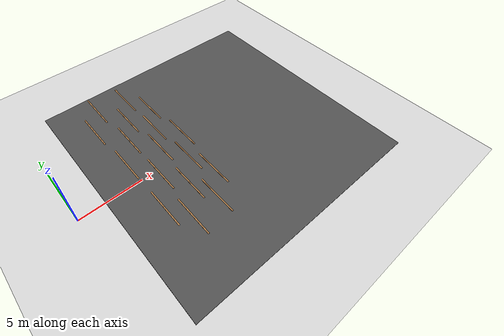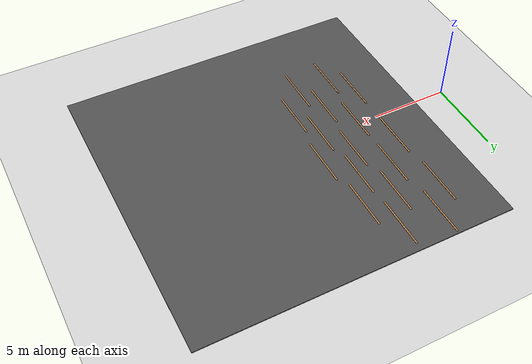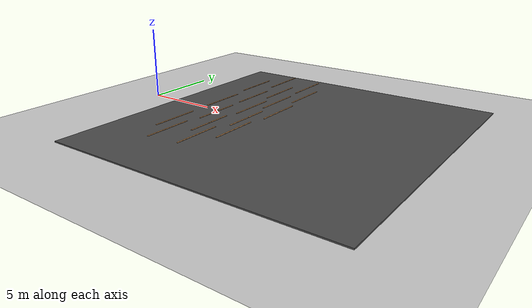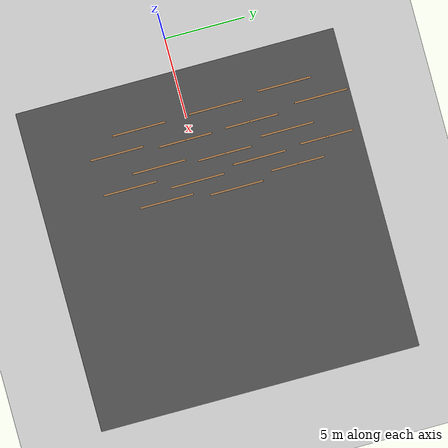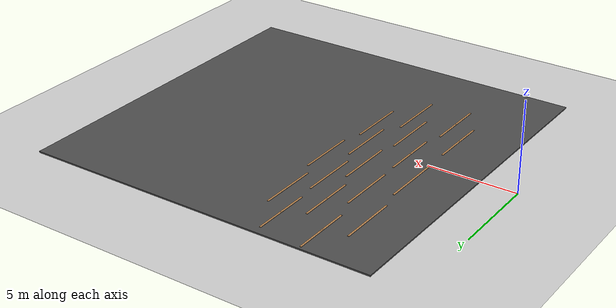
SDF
<sdf version="1.7">
 <world name="default">
  <light name="sun" type="directional">
   <pose>0 0 10 0 -0 0</pose>
   <diffuse>0.8 0.8 0.8 1</diffuse>
   <specular>0.2 0.2 0.2 1</specular>
   <attenuation>
    <range>1000</range>
    <constant>0.9</constant>
    <linear>0.01</linear>
    <quadratic>0.001</quadratic>
   </attenuation>
   <direction>-0.5 0.1 -0.9</direction>
   <spot><inner_angle>0</inner_angle><outer_angle>0</outer_angle><falloff>0</falloff></spot>
  </light>
  <model name="ground_plane">
   <static>1</static>
   <link name="link">
    <collision name="collision">
     <geometry><plane><normal>0 0 1</normal><size>100 100</size></plane></geometry>
     <surface><friction><ode><mu>100</mu><mu2>50</mu2></ode></friction></surface>
    </collision>
    <visual name="visual">
     <cast_shadows>0</cast_shadows>
     <geometry><plane><normal>0 0 1</normal><size>100 100</size></plane></geometry>
     <material>
      <script><uri>file://media/materials/scripts/gazebo.material</uri><name>Gazebo/Grey</name></script>
     </material>
    </visual>
   </link>
  </model>
  <gravity>0 0 -9.8</gravity>
  <magnetic_field>6e-06 2.3e-05 -4.2e-05</magnetic_field>
  <atmosphere type="adiabatic"/>
  <physics type="ode">
   <max_step_size>0.001</max_step_size>
   <real_time_factor>1</real_time_factor>
   <real_time_update_rate>1000</real_time_update_rate>
  </physics>
  <scene><ambient>0.4 0.4 0.4 1</ambient><background>0.7 0.7 0.7 1</background><shadows>1</shadows></scene>
  <spherical_coordinates>
   <surface_model>EARTH_WGS84</surface_model>
   <latitude_deg>0</latitude_deg>
   <longitude_deg>0</longitude_deg>
   <elevation>0</elevation>
   <heading_deg>0</heading_deg>
  </spherical_coordinates>
  <model name="asphalt_plane">
   <static>1</static>
   <link name="link">
    <collision name="collision"><geometry><box><size>20 20 0.1</size></box></geometry></collision>
    <visual name="visual">
     <cast_shadows>0</cast_shadows>
     <geometry><box><size>20 20 0.1</size></box></geometry>
     <material>
      <script>
       <uri>model://asphalt_plane/materials/scripts</uri>
       <uri>model://asphalt_plane/materials/textures</uri>
       <name>vrc/asphalt</name>
      </script>
     </material>
    </visual>
   </link>
   <pose>12.0553 0.030976 0 0 -0 0</pose>
  </model>
  <model name="wooden_board4">
   <link name="base">
    <pose>-0 -0 0.00523 0 -0 0</pose>
    <inertial>
     <mass>0.2765</mass>
     <inertia>
      <ixx>0.0025148</ixx>
      <ixy>0</ixy>
      <ixz>0</ixz>
      <iyy>0.00024037</iyy>
      <iyz>0</iyz>
      <izz>0.00275013</izz>
     </inertia>
    </inertial>
    <visual name="visual">
     <geometry><box><size>0.1016 3.3302 0.02046</size></box></geometry>
     <material>
      <script><uri>file://media/materials/scripts/gazebo.material</uri><name>Gazebo/Wood</name></script>
      <shader type="pixel"><normal_map>__default__</normal_map></shader>
      <ambient>1 1 1 1</ambient>
      <diffuse>1 1 1 1</diffuse>
      <specular>0.2 0.2 0.2 1</specular>
      <emissive>0 0 0 1</emissive>
     </material>
    </visual>
    <visual name="tee_nut_1">
     <pose>0 -0.116 0 0 -0 0</pose>
     <geometry><cylinder><radius>0.00635</radius><length>0.020565</length></cylinder></geometry>
     <material>
      <script><uri>file://media/materials/scripts/gazebo.material</uri><name>Gazebo/Grey</name></script>
      <shader type="pixel"><normal_map>__default__</normal_map></shader>
      <ambient>0.3 0.3 0.3 1</ambient>
      <diffuse>0.7 0.7 0.7 1</diffuse>
      <specular>0.01 0.01 0.01 1</specular>
      <emissive>0 0 0 1</emissive>
     </material>
    </visual>
    <visual name="tee_nut_3">
     <pose>0 0.038 0 0 -0 0</pose>
     <geometry><cylinder><radius>0.00635</radius><length>0.020565</length></cylinder></geometry>
     <material>
      <script><uri>file://media/materials/scripts/gazebo.material</uri><name>Gazebo/Grey</name></script>
      <shader type="pixel"><normal_map>__default__</normal_map></shader>
      <ambient>0.3 0.3 0.3 1</ambient>
      <diffuse>0.7 0.7 0.7 1</diffuse>
      <specular>0.01 0.01 0.01 1</specular>
      <emissive>0 0 0 1</emissive>
     </material>
    </visual>
    <visual name="tee_nut_2">
     <pose>0 -0.038 0 0 -0 0</pose>
     <geometry><cylinder><radius>0.00635</radius><length>0.020565</length></cylinder></geometry>
     <material>
      <script><uri>file://media/materials/scripts/gazebo.material</uri><name>Gazebo/Grey</name></script>
      <shader type="pixel"><normal_map>__default__</normal_map></shader>
      <ambient>0.3 0.3 0.3 1</ambient>
      <diffuse>0.7 0.7 0.7 1</diffuse>
      <specular>0.01 0.01 0.01 1</specular>
      <emissive>0 0 0 1</emissive>
     </material>
    </visual>
    <visual name="tee_nut_4">
     <pose>0 0.116 0 0 -0 0</pose>
     <geometry><cylinder><radius>0.00635</radius><length>0.020565</length></cylinder></geometry>
     <material>
      <script><uri>file://media/materials/scripts/gazebo.material</uri><name>Gazebo/Grey</name></script>
      <shader type="pixel"><normal_map>__default__</normal_map></shader>
      <ambient>0.3 0.3 0.3 1</ambient>
      <diffuse>0.7 0.7 0.7 1</diffuse>
      <specular>0.01 0.01 0.01 1</specular>
      <emissive>0 0 0 1</emissive>
     </material>
    </visual>
    <collision name="collision">
     <geometry><box><size>0.1016 0.3302 0.04046</size></box></geometry>
     <surface>
      <friction>
       <ode><mu>1</mu><mu2>1</mu2><fdir1>0 0 0</fdir1><slip1>0</slip1><slip2>0</slip2></ode>
       <torsional>
        <coefficient>1</coefficient>
        <patch_radius>0</patch_radius>
        <surface_radius>0.01</surface_radius>
        <use_patch_radius>0</use_patch_radius>
        <ode><slip>0</slip></ode>
       </torsional>
      </friction>
      <bounce><restitution_coefficient>0</restitution_coefficient><threshold>1e+06</threshold></bounce>
      <contact>
       <collide_without_contact>0</collide_without_contact>
       <collide_without_contact_bitmask>1</collide_without_contact_bitmask>
       <collide_bitmask>1</collide_bitmask>
       <ode>
        <soft_cfm>0</soft_cfm>
        <soft_erp>0.2</soft_erp>
        <kp>100000</kp>
        <kd>100</kd>
        <max_vel>100</max_vel>
        <min_depth>0.001</min_depth>
       </ode>
       <bullet>
        <split_impulse>1</split_impulse>
        <split_impulse_penetration_threshold>-0.01</split_impulse_penetration_threshold>
        <soft_cfm>0</soft_cfm>
        <soft_erp>0.2</soft_erp>
        <kp>100000</kp>
        <kd>100</kd>
       </bullet>
      </contact>
     </surface>
    </collision>
   </link>
   <static>0</static>
   <pose>4.89768 -2.95722 0.063993 0 -0 2.5e-05</pose>
  </model>
  <model name="wooden_board4_0">
   <link name="base">
    <pose>-0 -0 0.00523 0 -0 0</pose>
    <inertial>
     <mass>0.2765</mass>
     <inertia>
      <ixx>0.0025148</ixx>
      <ixy>0</ixy>
      <ixz>0</ixz>
      <iyy>0.00024037</iyy>
      <iyz>0</iyz>
      <izz>0.00275013</izz>
     </inertia>
    </inertial>
    <visual name="visual">
     <geometry><box><size>0.1016 3.3302 0.02046</size></box></geometry>
     <material>
      <script><uri>file://media/materials/scripts/gazebo.material</uri><name>Gazebo/Wood</name></script>
      <shader type="pixel"><normal_map>__default__</normal_map></shader>
      <ambient>1 1 1 1</ambient>
      <diffuse>1 1 1 1</diffuse>
      <specular>0.2 0.2 0.2 1</specular>
      <emissive>0 0 0 1</emissive>
     </material>
    </visual>
    <visual name="tee_nut_1">
     <pose>0 -0.116 0 0 -0 0</pose>
     <geometry><cylinder><radius>0.00635</radius><length>0.020565</length></cylinder></geometry>
     <material>
      <script><uri>file://media/materials/scripts/gazebo.material</uri><name>Gazebo/Grey</name></script>
      <shader type="pixel"><normal_map>__default__</normal_map></shader>
      <ambient>0.3 0.3 0.3 1</ambient>
      <diffuse>0.7 0.7 0.7 1</diffuse>
      <specular>0.01 0.01 0.01 1</specular>
      <emissive>0 0 0 1</emissive>
     </material>
    </visual>
    <visual name="tee_nut_3">
     <pose>0 0.038 0 0 -0 0</pose>
     <geometry><cylinder><radius>0.00635</radius><length>0.020565</length></cylinder></geometry>
     <material>
      <script><uri>file://media/materials/scripts/gazebo.material</uri><name>Gazebo/Grey</name></script>
      <shader type="pixel"><normal_map>__default__</normal_map></shader>
      <ambient>0.3 0.3 0.3 1</ambient>
      <diffuse>0.7 0.7 0.7 1</diffuse>
      <specular>0.01 0.01 0.01 1</specular>
      <emissive>0 0 0 1</emissive>
     </material>
    </visual>
    <visual name="tee_nut_2">
     <pose>0 -0.038 0 0 -0 0</pose>
     <geometry><cylinder><radius>0.00635</radius><length>0.020565</length></cylinder></geometry>
     <material>
      <script><uri>file://media/materials/scripts/gazebo.material</uri><name>Gazebo/Grey</name></script>
      <shader type="pixel"><normal_map>__default__</normal_map></shader>
      <ambient>0.3 0.3 0.3 1</ambient>
      <diffuse>0.7 0.7 0.7 1</diffuse>
      <specular>0.01 0.01 0.01 1</specular>
      <emissive>0 0 0 1</emissive>
     </material>
    </visual>
    <visual name="tee_nut_4">
     <pose>0 0.116 0 0 -0 0</pose>
     <geometry><cylinder><radius>0.00635</radius><length>0.020565</length></cylinder></geometry>
     <material>
      <script><uri>file://media/materials/scripts/gazebo.material</uri><name>Gazebo/Grey</name></script>
      <shader type="pixel"><normal_map>__default__</normal_map></shader>
      <ambient>0.3 0.3 0.3 1</ambient>
      <diffuse>0.7 0.7 0.7 1</diffuse>
      <specular>0.01 0.01 0.01 1</specular>
      <emissive>0 0 0 1</emissive>
     </material>
    </visual>
    <collision name="collision">
     <geometry><box><size>0.1016 0.3302 0.04046</size></box></geometry>
     <surface>
      <friction>
       <ode><mu>1</mu><mu2>1</mu2><fdir1>0 0 0</fdir1><slip1>0</slip1><slip2>0</slip2></ode>
       <torsional>
        <coefficient>1</coefficient>
        <patch_radius>0</patch_radius>
        <surface_radius>0.01</surface_radius>
        <use_patch_radius>0</use_patch_radius>
        <ode><slip>0</slip></ode>
       </torsional>
      </friction>
      <bounce><restitution_coefficient>0</restitution_coefficient><threshold>1e+06</threshold></bounce>
      <contact>
       <collide_without_contact>0</collide_without_contact>
       <collide_without_contact_bitmask>1</collide_without_contact_bitmask>
       <collide_bitmask>1</collide_bitmask>
       <ode>
        <soft_cfm>0</soft_cfm>
        <soft_erp>0.2</soft_erp>
        <kp>100000</kp>
        <kd>100</kd>
        <max_vel>100</max_vel>
        <min_depth>0.001</min_depth>
       </ode>
       <bullet>
        <split_impulse>1</split_impulse>
        <split_impulse_penetration_threshold>-0.01</split_impulse_penetration_threshold>
        <soft_cfm>0</soft_cfm>
        <soft_erp>0.2</soft_erp>
        <kp>100000</kp>
        <kd>100</kd>
       </bullet>
      </contact>
     </surface>
    </collision>
   </link>
   <static>0</static>
   <pose>4.83829 1.88469 0.063993 0 -0 2.5e-05</pose>
  </model>
  <model name="wooden_board4_1">
   <link name="base">
    <pose>-0 -0 0.00523 0 -0 0</pose>
    <inertial>
     <mass>0.2765</mass>
     <inertia>
      <ixx>0.0025148</ixx>
      <ixy>0</ixy>
      <ixz>0</ixz>
      <iyy>0.00024037</iyy>
      <iyz>0</iyz>
      <izz>0.00275013</izz>
     </inertia>
    </inertial>
    <visual name="visual">
     <geometry><box><size>0.1016 3.3302 0.02046</size></box></geometry>
     <material>
      <script><uri>file://media/materials/scripts/gazebo.material</uri><name>Gazebo/Wood</name></script>
      <shader type="pixel"><normal_map>__default__</normal_map></shader>
      <ambient>1 1 1 1</ambient>
      <diffuse>1 1 1 1</diffuse>
      <specular>0.2 0.2 0.2 1</specular>
      <emissive>0 0 0 1</emissive>
     </material>
    </visual>
    <visual name="tee_nut_1">
     <pose>0 -0.116 0 0 -0 0</pose>
     <geometry><cylinder><radius>0.00635</radius><length>0.020565</length></cylinder></geometry>
     <material>
      <script><uri>file://media/materials/scripts/gazebo.material</uri><name>Gazebo/Grey</name></script>
      <shader type="pixel"><normal_map>__default__</normal_map></shader>
      <ambient>0.3 0.3 0.3 1</ambient>
      <diffuse>0.7 0.7 0.7 1</diffuse>
      <specular>0.01 0.01 0.01 1</specular>
      <emissive>0 0 0 1</emissive>
     </material>
    </visual>
    <visual name="tee_nut_3">
     <pose>0 0.038 0 0 -0 0</pose>
     <geometry><cylinder><radius>0.00635</radius><length>0.020565</length></cylinder></geometry>
     <material>
      <script><uri>file://media/materials/scripts/gazebo.material</uri><name>Gazebo/Grey</name></script>
      <shader type="pixel"><normal_map>__default__</normal_map></shader>
      <ambient>0.3 0.3 0.3 1</ambient>
      <diffuse>0.7 0.7 0.7 1</diffuse>
      <specular>0.01 0.01 0.01 1</specular>
      <emissive>0 0 0 1</emissive>
     </material>
    </visual>
    <visual name="tee_nut_2">
     <pose>0 -0.038 0 0 -0 0</pose>
     <geometry><cylinder><radius>0.00635</radius><length>0.020565</length></cylinder></geometry>
     <material>
      <script><uri>file://media/materials/scripts/gazebo.material</uri><name>Gazebo/Grey</name></script>
      <shader type="pixel"><normal_map>__default__</normal_map></shader>
      <ambient>0.3 0.3 0.3 1</ambient>
      <diffuse>0.7 0.7 0.7 1</diffuse>
      <specular>0.01 0.01 0.01 1</specular>
      <emissive>0 0 0 1</emissive>
     </material>
    </visual>
    <visual name="tee_nut_4">
     <pose>0 0.116 0 0 -0 0</pose>
     <geometry><cylinder><radius>0.00635</radius><length>0.020565</length></cylinder></geometry>
     <material>
      <script><uri>file://media/materials/scripts/gazebo.material</uri><name>Gazebo/Grey</name></script>
      <shader type="pixel"><normal_map>__default__</normal_map></shader>
      <ambient>0.3 0.3 0.3 1</ambient>
      <diffuse>0.7 0.7 0.7 1</diffuse>
      <specular>0.01 0.01 0.01 1</specular>
      <emissive>0 0 0 1</emissive>
     </material>
    </visual>
    <collision name="collision">
     <geometry><box><size>0.1016 0.3302 0.04046</size></box></geometry>
     <surface>
      <friction>
       <ode><mu>1</mu><mu2>1</mu2><fdir1>0 0 0</fdir1><slip1>0</slip1><slip2>0</slip2></ode>
       <torsional>
        <coefficient>1</coefficient>
        <patch_radius>0</patch_radius>
        <surface_radius>0.01</surface_radius>
        <use_patch_radius>0</use_patch_radius>
        <ode><slip>0</slip></ode>
       </torsional>
      </friction>
      <bounce><restitution_coefficient>0</restitution_coefficient><threshold>1e+06</threshold></bounce>
      <contact>
       <collide_without_contact>0</collide_without_contact>
       <collide_without_contact_bitmask>1</collide_without_contact_bitmask>
       <collide_bitmask>1</collide_bitmask>
       <ode>
        <soft_cfm>0</soft_cfm>
        <soft_erp>0.2</soft_erp>
        <kp>100000</kp>
        <kd>100</kd>
        <max_vel>100</max_vel>
        <min_depth>0.001</min_depth>
       </ode>
       <bullet>
        <split_impulse>1</split_impulse>
        <split_impulse_penetration_threshold>-0.01</split_impulse_penetration_threshold>
        <soft_cfm>0</soft_cfm>
        <soft_erp>0.2</soft_erp>
        <kp>100000</kp>
        <kd>100</kd>
       </bullet>
      </contact>
     </surface>
    </collision>
   </link>
   <static>0</static>
   <pose>6.2785 -0.414987 0.063993 0 -0 2.5e-05</pose>
  </model>
  <model name="wooden_board4_2">
   <link name="base">
    <pose>-0 -0 0.00523 0 -0 0</pose>
    <inertial>
     <mass>0.2765</mass>
     <inertia>
      <ixx>0.0025148</ixx>
      <ixy>0</ixy>
      <ixz>0</ixz>
      <iyy>0.00024037</iyy>
      <iyz>0</iyz>
      <izz>0.00275013</izz>
     </inertia>
    </inertial>
    <visual name="visual">
     <geometry><box><size>0.1016 3.3302 0.02046</size></box></geometry>
     <material>
      <script><uri>file://media/materials/scripts/gazebo.material</uri><name>Gazebo/Wood</name></script>
      <shader type="pixel"><normal_map>__default__</normal_map></shader>
      <ambient>1 1 1 1</ambient>
      <diffuse>1 1 1 1</diffuse>
      <specular>0.2 0.2 0.2 1</specular>
      <emissive>0 0 0 1</emissive>
     </material>
    </visual>
    <visual name="tee_nut_1">
     <pose>0 -0.116 0 0 -0 0</pose>
     <geometry><cylinder><radius>0.00635</radius><length>0.020565</length></cylinder></geometry>
     <material>
      <script><uri>file://media/materials/scripts/gazebo.material</uri><name>Gazebo/Grey</name></script>
      <shader type="pixel"><normal_map>__default__</normal_map></shader>
      <ambient>0.3 0.3 0.3 1</ambient>
      <diffuse>0.7 0.7 0.7 1</diffuse>
      <specular>0.01 0.01 0.01 1</specular>
      <emissive>0 0 0 1</emissive>
     </material>
    </visual>
    <visual name="tee_nut_3">
     <pose>0 0.038 0 0 -0 0</pose>
     <geometry><cylinder><radius>0.00635</radius><length>0.020565</length></cylinder></geometry>
     <material>
      <script><uri>file://media/materials/scripts/gazebo.material</uri><name>Gazebo/Grey</name></script>
      <shader type="pixel"><normal_map>__default__</normal_map></shader>
      <ambient>0.3 0.3 0.3 1</ambient>
      <diffuse>0.7 0.7 0.7 1</diffuse>
      <specular>0.01 0.01 0.01 1</specular>
      <emissive>0 0 0 1</emissive>
     </material>
    </visual>
    <visual name="tee_nut_2">
     <pose>0 -0.038 0 0 -0 0</pose>
     <geometry><cylinder><radius>0.00635</radius><length>0.020565</length></cylinder></geometry>
     <material>
      <script><uri>file://media/materials/scripts/gazebo.material</uri><name>Gazebo/Grey</name></script>
      <shader type="pixel"><normal_map>__default__</normal_map></shader>
      <ambient>0.3 0.3 0.3 1</ambient>
      <diffuse>0.7 0.7 0.7 1</diffuse>
      <specular>0.01 0.01 0.01 1</specular>
      <emissive>0 0 0 1</emissive>
     </material>
    </visual>
    <visual name="tee_nut_4">
     <pose>0 0.116 0 0 -0 0</pose>
     <geometry><cylinder><radius>0.00635</radius><length>0.020565</length></cylinder></geometry>
     <material>
      <script><uri>file://media/materials/scripts/gazebo.material</uri><name>Gazebo/Grey</name></script>
      <shader type="pixel"><normal_map>__default__</normal_map></shader>
      <ambient>0.3 0.3 0.3 1</ambient>
      <diffuse>0.7 0.7 0.7 1</diffuse>
      <specular>0.01 0.01 0.01 1</specular>
      <emissive>0 0 0 1</emissive>
     </material>
    </visual>
    <collision name="collision">
     <geometry><box><size>0.1016 0.3302 0.04046</size></box></geometry>
     <surface>
      <friction>
       <ode><mu>1</mu><mu2>1</mu2><fdir1>0 0 0</fdir1><slip1>0</slip1><slip2>0</slip2></ode>
       <torsional>
        <coefficient>1</coefficient>
        <patch_radius>0</patch_radius>
        <surface_radius>0.01</surface_radius>
        <use_patch_radius>0</use_patch_radius>
        <ode><slip>0</slip></ode>
       </torsional>
      </friction>
      <bounce><restitution_coefficient>0</restitution_coefficient><threshold>1e+06</threshold></bounce>
      <contact>
       <collide_without_contact>0</collide_without_contact>
       <collide_without_contact_bitmask>1</collide_without_contact_bitmask>
       <collide_bitmask>1</collide_bitmask>
       <ode>
        <soft_cfm>0</soft_cfm>
        <soft_erp>0.2</soft_erp>
        <kp>100000</kp>
        <kd>100</kd>
        <max_vel>100</max_vel>
        <min_depth>0.001</min_depth>
       </ode>
       <bullet>
        <split_impulse>1</split_impulse>
        <split_impulse_penetration_threshold>-0.01</split_impulse_penetration_threshold>
        <soft_cfm>0</soft_cfm>
        <soft_erp>0.2</soft_erp>
        <kp>100000</kp>
        <kd>100</kd>
       </bullet>
      </contact>
     </surface>
    </collision>
   </link>
   <static>0</static>
   <pose>4.57081 6.26673 0.063993 0 -0 2.5e-05</pose>
  </model>
  <model name="wooden_board4_3">
   <link name="base">
    <pose>-0 -0 0.00523 0 -0 0</pose>
    <inertial>
     <mass>0.2765</mass>
     <inertia>
      <ixx>0.0025148</ixx>
      <ixy>0</ixy>
      <ixz>0</ixz>
      <iyy>0.00024037</iyy>
      <iyz>0</iyz>
      <izz>0.00275013</izz>
     </inertia>
    </inertial>
    <visual name="visual">
     <geometry><box><size>0.1016 3.3302 0.02046</size></box></geometry>
     <material>
      <script><uri>file://media/materials/scripts/gazebo.material</uri><name>Gazebo/Wood</name></script>
      <shader type="pixel"><normal_map>__default__</normal_map></shader>
      <ambient>1 1 1 1</ambient>
      <diffuse>1 1 1 1</diffuse>
      <specular>0.2 0.2 0.2 1</specular>
      <emissive>0 0 0 1</emissive>
     </material>
    </visual>
    <visual name="tee_nut_1">
     <pose>0 -0.116 0 0 -0 0</pose>
     <geometry><cylinder><radius>0.00635</radius><length>0.020565</length></cylinder></geometry>
     <material>
      <script><uri>file://media/materials/scripts/gazebo.material</uri><name>Gazebo/Grey</name></script>
      <shader type="pixel"><normal_map>__default__</normal_map></shader>
      <ambient>0.3 0.3 0.3 1</ambient>
      <diffuse>0.7 0.7 0.7 1</diffuse>
      <specular>0.01 0.01 0.01 1</specular>
      <emissive>0 0 0 1</emissive>
     </material>
    </visual>
    <visual name="tee_nut_3">
     <pose>0 0.038 0 0 -0 0</pose>
     <geometry><cylinder><radius>0.00635</radius><length>0.020565</length></cylinder></geometry>
     <material>
      <script><uri>file://media/materials/scripts/gazebo.material</uri><name>Gazebo/Grey</name></script>
      <shader type="pixel"><normal_map>__default__</normal_map></shader>
      <ambient>0.3 0.3 0.3 1</ambient>
      <diffuse>0.7 0.7 0.7 1</diffuse>
      <specular>0.01 0.01 0.01 1</specular>
      <emissive>0 0 0 1</emissive>
     </material>
    </visual>
    <visual name="tee_nut_2">
     <pose>0 -0.038 0 0 -0 0</pose>
     <geometry><cylinder><radius>0.00635</radius><length>0.020565</length></cylinder></geometry>
     <material>
      <script><uri>file://media/materials/scripts/gazebo.material</uri><name>Gazebo/Grey</name></script>
      <shader type="pixel"><normal_map>__default__</normal_map></shader>
      <ambient>0.3 0.3 0.3 1</ambient>
      <diffuse>0.7 0.7 0.7 1</diffuse>
      <specular>0.01 0.01 0.01 1</specular>
      <emissive>0 0 0 1</emissive>
     </material>
    </visual>
    <visual name="tee_nut_4">
     <pose>0 0.116 0 0 -0 0</pose>
     <geometry><cylinder><radius>0.00635</radius><length>0.020565</length></cylinder></geometry>
     <material>
      <script><uri>file://media/materials/scripts/gazebo.material</uri><name>Gazebo/Grey</name></script>
      <shader type="pixel"><normal_map>__default__</normal_map></shader>
      <ambient>0.3 0.3 0.3 1</ambient>
      <diffuse>0.7 0.7 0.7 1</diffuse>
      <specular>0.01 0.01 0.01 1</specular>
      <emissive>0 0 0 1</emissive>
     </material>
    </visual>
    <collision name="collision">
     <geometry><box><size>0.1016 0.3302 0.04046</size></box></geometry>
     <surface>
      <friction>
       <ode><mu>1</mu><mu2>1</mu2><fdir1>0 0 0</fdir1><slip1>0</slip1><slip2>0</slip2></ode>
       <torsional>
        <coefficient>1</coefficient>
        <patch_radius>0</patch_radius>
        <surface_radius>0.01</surface_radius>
        <use_patch_radius>0</use_patch_radius>
        <ode><slip>0</slip></ode>
       </torsional>
      </friction>
      <bounce><restitution_coefficient>0</restitution_coefficient><threshold>1e+06</threshold></bounce>
      <contact>
       <collide_without_contact>0</collide_without_contact>
       <collide_without_contact_bitmask>1</collide_without_contact_bitmask>
       <collide_bitmask>1</collide_bitmask>
       <ode>
        <soft_cfm>0</soft_cfm>
        <soft_erp>0.2</soft_erp>
        <kp>100000</kp>
        <kd>100</kd>
        <max_vel>100</max_vel>
        <min_depth>0.001</min_depth>
       </ode>
       <bullet>
        <split_impulse>1</split_impulse>
        <split_impulse_penetration_threshold>-0.01</split_impulse_penetration_threshold>
        <soft_cfm>0</soft_cfm>
        <soft_erp>0.2</soft_erp>
        <kp>100000</kp>
        <kd>100</kd>
       </bullet>
      </contact>
     </surface>
    </collision>
   </link>
   <static>0</static>
   <pose>6.21764 3.78263 0.063993 0 -0 2.5e-05</pose>
  </model>
  <model name="wooden_board4_4">
   <link name="base">
    <pose>-0 -0 0.00523 0 -0 0</pose>
    <inertial>
     <mass>0.2765</mass>
     <inertia>
      <ixx>0.0025148</ixx>
      <ixy>0</ixy>
      <ixz>0</ixz>
      <iyy>0.00024037</iyy>
      <iyz>0</iyz>
      <izz>0.00275013</izz>
     </inertia>
    </inertial>
    <visual name="visual">
     <geometry><box><size>0.1016 3.3302 0.02046</size></box></geometry>
     <material>
      <script><uri>file://media/materials/scripts/gazebo.material</uri><name>Gazebo/Wood</name></script>
      <shader type="pixel"><normal_map>__default__</normal_map></shader>
      <ambient>1 1 1 1</ambient>
      <diffuse>1 1 1 1</diffuse>
      <specular>0.2 0.2 0.2 1</specular>
      <emissive>0 0 0 1</emissive>
     </material>
    </visual>
    <visual name="tee_nut_1">
     <pose>0 -0.116 0 0 -0 0</pose>
     <geometry><cylinder><radius>0.00635</radius><length>0.020565</length></cylinder></geometry>
     <material>
      <script><uri>file://media/materials/scripts/gazebo.material</uri><name>Gazebo/Grey</name></script>
      <shader type="pixel"><normal_map>__default__</normal_map></shader>
      <ambient>0.3 0.3 0.3 1</ambient>
      <diffuse>0.7 0.7 0.7 1</diffuse>
      <specular>0.01 0.01 0.01 1</specular>
      <emissive>0 0 0 1</emissive>
     </material>
    </visual>
    <visual name="tee_nut_3">
     <pose>0 0.038 0 0 -0 0</pose>
     <geometry><cylinder><radius>0.00635</radius><length>0.020565</length></cylinder></geometry>
     <material>
      <script><uri>file://media/materials/scripts/gazebo.material</uri><name>Gazebo/Grey</name></script>
      <shader type="pixel"><normal_map>__default__</normal_map></shader>
      <ambient>0.3 0.3 0.3 1</ambient>
      <diffuse>0.7 0.7 0.7 1</diffuse>
      <specular>0.01 0.01 0.01 1</specular>
      <emissive>0 0 0 1</emissive>
     </material>
    </visual>
    <visual name="tee_nut_2">
     <pose>0 -0.038 0 0 -0 0</pose>
     <geometry><cylinder><radius>0.00635</radius><length>0.020565</length></cylinder></geometry>
     <material>
      <script><uri>file://media/materials/scripts/gazebo.material</uri><name>Gazebo/Grey</name></script>
      <shader type="pixel"><normal_map>__default__</normal_map></shader>
      <ambient>0.3 0.3 0.3 1</ambient>
      <diffuse>0.7 0.7 0.7 1</diffuse>
      <specular>0.01 0.01 0.01 1</specular>
      <emissive>0 0 0 1</emissive>
     </material>
    </visual>
    <visual name="tee_nut_4">
     <pose>0 0.116 0 0 -0 0</pose>
     <geometry><cylinder><radius>0.00635</radius><length>0.020565</length></cylinder></geometry>
     <material>
      <script><uri>file://media/materials/scripts/gazebo.material</uri><name>Gazebo/Grey</name></script>
      <shader type="pixel"><normal_map>__default__</normal_map></shader>
      <ambient>0.3 0.3 0.3 1</ambient>
      <diffuse>0.7 0.7 0.7 1</diffuse>
      <specular>0.01 0.01 0.01 1</specular>
      <emissive>0 0 0 1</emissive>
     </material>
    </visual>
    <collision name="collision">
     <geometry><box><size>0.1016 0.3302 0.04046</size></box></geometry>
     <surface>
      <friction>
       <ode><mu>1</mu><mu2>1</mu2><fdir1>0 0 0</fdir1><slip1>0</slip1><slip2>0</slip2></ode>
       <torsional>
        <coefficient>1</coefficient>
        <patch_radius>0</patch_radius>
        <surface_radius>0.01</surface_radius>
        <use_patch_radius>0</use_patch_radius>
        <ode><slip>0</slip></ode>
       </torsional>
      </friction>
      <bounce><restitution_coefficient>0</restitution_coefficient><threshold>1e+06</threshold></bounce>
      <contact>
       <collide_without_contact>0</collide_without_contact>
       <collide_without_contact_bitmask>1</collide_without_contact_bitmask>
       <collide_bitmask>1</collide_bitmask>
       <ode>
        <soft_cfm>0</soft_cfm>
        <soft_erp>0.2</soft_erp>
        <kp>100000</kp>
        <kd>100</kd>
        <max_vel>100</max_vel>
        <min_depth>0.001</min_depth>
       </ode>
       <bullet>
        <split_impulse>1</split_impulse>
        <split_impulse_penetration_threshold>-0.01</split_impulse_penetration_threshold>
        <soft_cfm>0</soft_cfm>
        <soft_erp>0.2</soft_erp>
        <kp>100000</kp>
        <kd>100</kd>
       </bullet>
      </contact>
     </surface>
    </collision>
   </link>
   <static>0</static>
   <pose>5.99368 -4.64442 0.063993 0 -0 2.5e-05</pose>
  </model>
  <model name="wooden_board4_5">
   <link name="base">
    <pose>-0 -0 0.00523 0 -0 0</pose>
    <inertial>
     <mass>0.2765</mass>
     <inertia>
      <ixx>0.0025148</ixx>
      <ixy>0</ixy>
      <ixz>0</ixz>
      <iyy>0.00024037</iyy>
      <iyz>0</iyz>
      <izz>0.00275013</izz>
     </inertia>
    </inertial>
    <visual name="visual">
     <geometry><box><size>0.1016 3.3302 0.02046</size></box></geometry>
     <material>
      <script><uri>file://media/materials/scripts/gazebo.material</uri><name>Gazebo/Wood</name></script>
      <shader type="pixel"><normal_map>__default__</normal_map></shader>
      <ambient>1 1 1 1</ambient>
      <diffuse>1 1 1 1</diffuse>
      <specular>0.2 0.2 0.2 1</specular>
      <emissive>0 0 0 1</emissive>
     </material>
    </visual>
    <visual name="tee_nut_1">
     <pose>0 -0.116 0 0 -0 0</pose>
     <geometry><cylinder><radius>0.00635</radius><length>0.020565</length></cylinder></geometry>
     <material>
      <script><uri>file://media/materials/scripts/gazebo.material</uri><name>Gazebo/Grey</name></script>
      <shader type="pixel"><normal_map>__default__</normal_map></shader>
      <ambient>0.3 0.3 0.3 1</ambient>
      <diffuse>0.7 0.7 0.7 1</diffuse>
      <specular>0.01 0.01 0.01 1</specular>
      <emissive>0 0 0 1</emissive>
     </material>
    </visual>
    <visual name="tee_nut_3">
     <pose>0 0.038 0 0 -0 0</pose>
     <geometry><cylinder><radius>0.00635</radius><length>0.020565</length></cylinder></geometry>
     <material>
      <script><uri>file://media/materials/scripts/gazebo.material</uri><name>Gazebo/Grey</name></script>
      <shader type="pixel"><normal_map>__default__</normal_map></shader>
      <ambient>0.3 0.3 0.3 1</ambient>
      <diffuse>0.7 0.7 0.7 1</diffuse>
      <specular>0.01 0.01 0.01 1</specular>
      <emissive>0 0 0 1</emissive>
     </material>
    </visual>
    <visual name="tee_nut_2">
     <pose>0 -0.038 0 0 -0 0</pose>
     <geometry><cylinder><radius>0.00635</radius><length>0.020565</length></cylinder></geometry>
     <material>
      <script><uri>file://media/materials/scripts/gazebo.material</uri><name>Gazebo/Grey</name></script>
      <shader type="pixel"><normal_map>__default__</normal_map></shader>
      <ambient>0.3 0.3 0.3 1</ambient>
      <diffuse>0.7 0.7 0.7 1</diffuse>
      <specular>0.01 0.01 0.01 1</specular>
      <emissive>0 0 0 1</emissive>
     </material>
    </visual>
    <visual name="tee_nut_4">
     <pose>0 0.116 0 0 -0 0</pose>
     <geometry><cylinder><radius>0.00635</radius><length>0.020565</length></cylinder></geometry>
     <material>
      <script><uri>file://media/materials/scripts/gazebo.material</uri><name>Gazebo/Grey</name></script>
      <shader type="pixel"><normal_map>__default__</normal_map></shader>
      <ambient>0.3 0.3 0.3 1</ambient>
      <diffuse>0.7 0.7 0.7 1</diffuse>
      <specular>0.01 0.01 0.01 1</specular>
      <emissive>0 0 0 1</emissive>
     </material>
    </visual>
    <collision name="collision">
     <geometry><box><size>0.1016 0.3302 0.04046</size></box></geometry>
     <surface>
      <friction>
       <ode><mu>1</mu><mu2>1</mu2><fdir1>0 0 0</fdir1><slip1>0</slip1><slip2>0</slip2></ode>
       <torsional>
        <coefficient>1</coefficient>
        <patch_radius>0</patch_radius>
        <surface_radius>0.01</surface_radius>
        <use_patch_radius>0</use_patch_radius>
        <ode><slip>0</slip></ode>
       </torsional>
      </friction>
      <bounce><restitution_coefficient>0</restitution_coefficient><threshold>1e+06</threshold></bounce>
      <contact>
       <collide_without_contact>0</collide_without_contact>
       <collide_without_contact_bitmask>1</collide_without_contact_bitmask>
       <collide_bitmask>1</collide_bitmask>
       <ode>
        <soft_cfm>0</soft_cfm>
        <soft_erp>0.2</soft_erp>
        <kp>100000</kp>
        <kd>100</kd>
        <max_vel>100</max_vel>
        <min_depth>0.001</min_depth>
       </ode>
       <bullet>
        <split_impulse>1</split_impulse>
        <split_impulse_penetration_threshold>-0.01</split_impulse_penetration_threshold>
        <soft_cfm>0</soft_cfm>
        <soft_erp>0.2</soft_erp>
        <kp>100000</kp>
        <kd>100</kd>
       </bullet>
      </contact>
     </surface>
    </collision>
   </link>
   <static>0</static>
   <pose>7.4396 -2.38898 0.063993 0 -0 2.5e-05</pose>
  </model>
  <model name="wooden_board4_6">
   <link name="base">
    <pose>-0 -0 0.00523 0 -0 0</pose>
    <inertial>
     <mass>0.2765</mass>
     <inertia>
      <ixx>0.0025148</ixx>
      <ixy>0</ixy>
      <ixz>0</ixz>
      <iyy>0.00024037</iyy>
      <iyz>0</iyz>
      <izz>0.00275013</izz>
     </inertia>
    </inertial>
    <visual name="visual">
     <geometry><box><size>0.1016 3.3302 0.02046</size></box></geometry>
     <material>
      <script><uri>file://media/materials/scripts/gazebo.material</uri><name>Gazebo/Wood</name></script>
      <shader type="pixel"><normal_map>__default__</normal_map></shader>
      <ambient>1 1 1 1</ambient>
      <diffuse>1 1 1 1</diffuse>
      <specular>0.2 0.2 0.2 1</specular>
      <emissive>0 0 0 1</emissive>
     </material>
    </visual>
    <visual name="tee_nut_1">
     <pose>0 -0.116 0 0 -0 0</pose>
     <geometry><cylinder><radius>0.00635</radius><length>0.020565</length></cylinder></geometry>
     <material>
      <script><uri>file://media/materials/scripts/gazebo.material</uri><name>Gazebo/Grey</name></script>
      <shader type="pixel"><normal_map>__default__</normal_map></shader>
      <ambient>0.3 0.3 0.3 1</ambient>
      <diffuse>0.7 0.7 0.7 1</diffuse>
      <specular>0.01 0.01 0.01 1</specular>
      <emissive>0 0 0 1</emissive>
     </material>
    </visual>
    <visual name="tee_nut_3">
     <pose>0 0.038 0 0 -0 0</pose>
     <geometry><cylinder><radius>0.00635</radius><length>0.020565</length></cylinder></geometry>
     <material>
      <script><uri>file://media/materials/scripts/gazebo.material</uri><name>Gazebo/Grey</name></script>
      <shader type="pixel"><normal_map>__default__</normal_map></shader>
      <ambient>0.3 0.3 0.3 1</ambient>
      <diffuse>0.7 0.7 0.7 1</diffuse>
      <specular>0.01 0.01 0.01 1</specular>
      <emissive>0 0 0 1</emissive>
     </material>
    </visual>
    <visual name="tee_nut_2">
     <pose>0 -0.038 0 0 -0 0</pose>
     <geometry><cylinder><radius>0.00635</radius><length>0.020565</length></cylinder></geometry>
     <material>
      <script><uri>file://media/materials/scripts/gazebo.material</uri><name>Gazebo/Grey</name></script>
      <shader type="pixel"><normal_map>__default__</normal_map></shader>
      <ambient>0.3 0.3 0.3 1</ambient>
      <diffuse>0.7 0.7 0.7 1</diffuse>
      <specular>0.01 0.01 0.01 1</specular>
      <emissive>0 0 0 1</emissive>
     </material>
    </visual>
    <visual name="tee_nut_4">
     <pose>0 0.116 0 0 -0 0</pose>
     <geometry><cylinder><radius>0.00635</radius><length>0.020565</length></cylinder></geometry>
     <material>
      <script><uri>file://media/materials/scripts/gazebo.material</uri><name>Gazebo/Grey</name></script>
      <shader type="pixel"><normal_map>__default__</normal_map></shader>
      <ambient>0.3 0.3 0.3 1</ambient>
      <diffuse>0.7 0.7 0.7 1</diffuse>
      <specular>0.01 0.01 0.01 1</specular>
      <emissive>0 0 0 1</emissive>
     </material>
    </visual>
    <collision name="collision">
     <geometry><box><size>0.1016 0.3302 0.04046</size></box></geometry>
     <surface>
      <friction>
       <ode><mu>1</mu><mu2>1</mu2><fdir1>0 0 0</fdir1><slip1>0</slip1><slip2>0</slip2></ode>
       <torsional>
        <coefficient>1</coefficient>
        <patch_radius>0</patch_radius>
        <surface_radius>0.01</surface_radius>
        <use_patch_radius>0</use_patch_radius>
        <ode><slip>0</slip></ode>
       </torsional>
      </friction>
      <bounce><restitution_coefficient>0</restitution_coefficient><threshold>1e+06</threshold></bounce>
      <contact>
       <collide_without_contact>0</collide_without_contact>
       <collide_without_contact_bitmask>1</collide_without_contact_bitmask>
       <collide_bitmask>1</collide_bitmask>
       <ode>
        <soft_cfm>0</soft_cfm>
        <soft_erp>0.2</soft_erp>
        <kp>100000</kp>
        <kd>100</kd>
        <max_vel>100</max_vel>
        <min_depth>0.001</min_depth>
       </ode>
       <bullet>
        <split_impulse>1</split_impulse>
        <split_impulse_penetration_threshold>-0.01</split_impulse_penetration_threshold>
        <soft_cfm>0</soft_cfm>
        <soft_erp>0.2</soft_erp>
        <kp>100000</kp>
        <kd>100</kd>
       </bullet>
      </contact>
     </surface>
    </collision>
   </link>
   <static>0</static>
   <pose>7.6964 1.67889 0.063993 0 -0 2.5e-05</pose>
  </model>
  <model name="wooden_board4_7">
   <link name="base">
    <pose>-0 -0 0.00523 0 -0 0</pose>
    <inertial>
     <mass>0.2765</mass>
     <inertia>
      <ixx>0.0025148</ixx>
      <ixy>0</ixy>
      <ixz>0</ixz>
      <iyy>0.00024037</iyy>
      <iyz>0</iyz>
      <izz>0.00275013</izz>
     </inertia>
    </inertial>
    <visual name="visual">
     <geometry><box><size>0.1016 3.3302 0.02046</size></box></geometry>
     <material>
      <script><uri>file://media/materials/scripts/gazebo.material</uri><name>Gazebo/Wood</name></script>
      <shader type="pixel"><normal_map>__default__</normal_map></shader>
      <ambient>1 1 1 1</ambient>
      <diffuse>1 1 1 1</diffuse>
      <specular>0.2 0.2 0.2 1</specular>
      <emissive>0 0 0 1</emissive>
     </material>
    </visual>
    <visual name="tee_nut_1">
     <pose>0 -0.116 0 0 -0 0</pose>
     <geometry><cylinder><radius>0.00635</radius><length>0.020565</length></cylinder></geometry>
     <material>
      <script><uri>file://media/materials/scripts/gazebo.material</uri><name>Gazebo/Grey</name></script>
      <shader type="pixel"><normal_map>__default__</normal_map></shader>
      <ambient>0.3 0.3 0.3 1</ambient>
      <diffuse>0.7 0.7 0.7 1</diffuse>
      <specular>0.01 0.01 0.01 1</specular>
      <emissive>0 0 0 1</emissive>
     </material>
    </visual>
    <visual name="tee_nut_3">
     <pose>0 0.038 0 0 -0 0</pose>
     <geometry><cylinder><radius>0.00635</radius><length>0.020565</length></cylinder></geometry>
     <material>
      <script><uri>file://media/materials/scripts/gazebo.material</uri><name>Gazebo/Grey</name></script>
      <shader type="pixel"><normal_map>__default__</normal_map></shader>
      <ambient>0.3 0.3 0.3 1</ambient>
      <diffuse>0.7 0.7 0.7 1</diffuse>
      <specular>0.01 0.01 0.01 1</specular>
      <emissive>0 0 0 1</emissive>
     </material>
    </visual>
    <visual name="tee_nut_2">
     <pose>0 -0.038 0 0 -0 0</pose>
     <geometry><cylinder><radius>0.00635</radius><length>0.020565</length></cylinder></geometry>
     <material>
      <script><uri>file://media/materials/scripts/gazebo.material</uri><name>Gazebo/Grey</name></script>
      <shader type="pixel"><normal_map>__default__</normal_map></shader>
      <ambient>0.3 0.3 0.3 1</ambient>
      <diffuse>0.7 0.7 0.7 1</diffuse>
      <specular>0.01 0.01 0.01 1</specular>
      <emissive>0 0 0 1</emissive>
     </material>
    </visual>
    <visual name="tee_nut_4">
     <pose>0 0.116 0 0 -0 0</pose>
     <geometry><cylinder><radius>0.00635</radius><length>0.020565</length></cylinder></geometry>
     <material>
      <script><uri>file://media/materials/scripts/gazebo.material</uri><name>Gazebo/Grey</name></script>
      <shader type="pixel"><normal_map>__default__</normal_map></shader>
      <ambient>0.3 0.3 0.3 1</ambient>
      <diffuse>0.7 0.7 0.7 1</diffuse>
      <specular>0.01 0.01 0.01 1</specular>
      <emissive>0 0 0 1</emissive>
     </material>
    </visual>
    <collision name="collision">
     <geometry><box><size>0.1016 0.3302 0.04046</size></box></geometry>
     <surface>
      <friction>
       <ode><mu>1</mu><mu2>1</mu2><fdir1>0 0 0</fdir1><slip1>0</slip1><slip2>0</slip2></ode>
       <torsional>
        <coefficient>1</coefficient>
        <patch_radius>0</patch_radius>
        <surface_radius>0.01</surface_radius>
        <use_patch_radius>0</use_patch_radius>
        <ode><slip>0</slip></ode>
       </torsional>
      </friction>
      <bounce><restitution_coefficient>0</restitution_coefficient><threshold>1e+06</threshold></bounce>
      <contact>
       <collide_without_contact>0</collide_without_contact>
       <collide_without_contact_bitmask>1</collide_without_contact_bitmask>
       <collide_bitmask>1</collide_bitmask>
       <ode>
        <soft_cfm>0</soft_cfm>
        <soft_erp>0.2</soft_erp>
        <kp>100000</kp>
        <kd>100</kd>
        <max_vel>100</max_vel>
        <min_depth>0.001</min_depth>
       </ode>
       <bullet>
        <split_impulse>1</split_impulse>
        <split_impulse_penetration_threshold>-0.01</split_impulse_penetration_threshold>
        <soft_cfm>0</soft_cfm>
        <soft_erp>0.2</soft_erp>
        <kp>100000</kp>
        <kd>100</kd>
       </bullet>
      </contact>
     </surface>
    </collision>
   </link>
   <static>0</static>
   <pose>7.26014 5.72105 0.063993 0 -0 2.5e-05</pose>
  </model>
  <model name="wooden_board4_8">
   <link name="base">
    <pose>-0 -0 0.00523 0 -0 0</pose>
    <inertial>
     <mass>0.2765</mass>
     <inertia>
      <ixx>0.0025148</ixx>
      <ixy>0</ixy>
      <ixz>0</ixz>
      <iyy>0.00024037</iyy>
      <iyz>0</iyz>
      <izz>0.00275013</izz>
     </inertia>
    </inertial>
    <visual name="visual">
     <geometry><box><size>0.1016 3.3302 0.02046</size></box></geometry>
     <material>
      <script><uri>file://media/materials/scripts/gazebo.material</uri><name>Gazebo/Wood</name></script>
      <shader type="pixel"><normal_map>__default__</normal_map></shader>
      <ambient>1 1 1 1</ambient>
      <diffuse>1 1 1 1</diffuse>
      <specular>0.2 0.2 0.2 1</specular>
      <emissive>0 0 0 1</emissive>
     </material>
    </visual>
    <visual name="tee_nut_1">
     <pose>0 -0.116 0 0 -0 0</pose>
     <geometry><cylinder><radius>0.00635</radius><length>0.020565</length></cylinder></geometry>
     <material>
      <script><uri>file://media/materials/scripts/gazebo.material</uri><name>Gazebo/Grey</name></script>
      <shader type="pixel"><normal_map>__default__</normal_map></shader>
      <ambient>0.3 0.3 0.3 1</ambient>
      <diffuse>0.7 0.7 0.7 1</diffuse>
      <specular>0.01 0.01 0.01 1</specular>
      <emissive>0 0 0 1</emissive>
     </material>
    </visual>
    <visual name="tee_nut_3">
     <pose>0 0.038 0 0 -0 0</pose>
     <geometry><cylinder><radius>0.00635</radius><length>0.020565</length></cylinder></geometry>
     <material>
      <script><uri>file://media/materials/scripts/gazebo.material</uri><name>Gazebo/Grey</name></script>
      <shader type="pixel"><normal_map>__default__</normal_map></shader>
      <ambient>0.3 0.3 0.3 1</ambient>
      <diffuse>0.7 0.7 0.7 1</diffuse>
      <specular>0.01 0.01 0.01 1</specular>
      <emissive>0 0 0 1</emissive>
     </material>
    </visual>
    <visual name="tee_nut_2">
     <pose>0 -0.038 0 0 -0 0</pose>
     <geometry><cylinder><radius>0.00635</radius><length>0.020565</length></cylinder></geometry>
     <material>
      <script><uri>file://media/materials/scripts/gazebo.material</uri><name>Gazebo/Grey</name></script>
      <shader type="pixel"><normal_map>__default__</normal_map></shader>
      <ambient>0.3 0.3 0.3 1</ambient>
      <diffuse>0.7 0.7 0.7 1</diffuse>
      <specular>0.01 0.01 0.01 1</specular>
      <emissive>0 0 0 1</emissive>
     </material>
    </visual>
    <visual name="tee_nut_4">
     <pose>0 0.116 0 0 -0 0</pose>
     <geometry><cylinder><radius>0.00635</radius><length>0.020565</length></cylinder></geometry>
     <material>
      <script><uri>file://media/materials/scripts/gazebo.material</uri><name>Gazebo/Grey</name></script>
      <shader type="pixel"><normal_map>__default__</normal_map></shader>
      <ambient>0.3 0.3 0.3 1</ambient>
      <diffuse>0.7 0.7 0.7 1</diffuse>
      <specular>0.01 0.01 0.01 1</specular>
      <emissive>0 0 0 1</emissive>
     </material>
    </visual>
    <collision name="collision">
     <geometry><box><size>0.1016 0.3302 0.04046</size></box></geometry>
     <surface>
      <friction>
       <ode><mu>1</mu><mu2>1</mu2><fdir1>0 0 0</fdir1><slip1>0</slip1><slip2>0</slip2></ode>
       <torsional>
        <coefficient>1</coefficient>
        <patch_radius>0</patch_radius>
        <surface_radius>0.01</surface_radius>
        <use_patch_radius>0</use_patch_radius>
        <ode><slip>0</slip></ode>
       </torsional>
      </friction>
      <bounce><restitution_coefficient>0</restitution_coefficient><threshold>1e+06</threshold></bounce>
      <contact>
       <collide_without_contact>0</collide_without_contact>
       <collide_without_contact_bitmask>1</collide_without_contact_bitmask>
       <collide_bitmask>1</collide_bitmask>
       <ode>
        <soft_cfm>0</soft_cfm>
        <soft_erp>0.2</soft_erp>
        <kp>100000</kp>
        <kd>100</kd>
        <max_vel>100</max_vel>
        <min_depth>0.001</min_depth>
       </ode>
       <bullet>
        <split_impulse>1</split_impulse>
        <split_impulse_penetration_threshold>-0.01</split_impulse_penetration_threshold>
        <soft_cfm>0</soft_cfm>
        <soft_erp>0.2</soft_erp>
        <kp>100000</kp>
        <kd>100</kd>
       </bullet>
      </contact>
     </surface>
    </collision>
   </link>
   <static>0</static>
   <pose>8.25494 -4.41197 0.063993 0 -0 2.5e-05</pose>
  </model>
  <model name="wooden_board4_9">
   <link name="base">
    <pose>-0 -0 0.00523 0 -0 0</pose>
    <inertial>
     <mass>0.2765</mass>
     <inertia>
      <ixx>0.0025148</ixx>
      <ixy>0</ixy>
      <ixz>0</ixz>
      <iyy>0.00024037</iyy>
      <iyz>0</iyz>
      <izz>0.00275013</izz>
     </inertia>
    </inertial>
    <visual name="visual">
     <geometry><box><size>0.1016 3.3302 0.02046</size></box></geometry>
     <material>
      <script><uri>file://media/materials/scripts/gazebo.material</uri><name>Gazebo/Wood</name></script>
      <shader type="pixel"><normal_map>__default__</normal_map></shader>
      <ambient>1 1 1 1</ambient>
      <diffuse>1 1 1 1</diffuse>
      <specular>0.2 0.2 0.2 1</specular>
      <emissive>0 0 0 1</emissive>
     </material>
    </visual>
    <visual name="tee_nut_1">
     <pose>0 -0.116 0 0 -0 0</pose>
     <geometry><cylinder><radius>0.00635</radius><length>0.020565</length></cylinder></geometry>
     <material>
      <script><uri>file://media/materials/scripts/gazebo.material</uri><name>Gazebo/Grey</name></script>
      <shader type="pixel"><normal_map>__default__</normal_map></shader>
      <ambient>0.3 0.3 0.3 1</ambient>
      <diffuse>0.7 0.7 0.7 1</diffuse>
      <specular>0.01 0.01 0.01 1</specular>
      <emissive>0 0 0 1</emissive>
     </material>
    </visual>
    <visual name="tee_nut_3">
     <pose>0 0.038 0 0 -0 0</pose>
     <geometry><cylinder><radius>0.00635</radius><length>0.020565</length></cylinder></geometry>
     <material>
      <script><uri>file://media/materials/scripts/gazebo.material</uri><name>Gazebo/Grey</name></script>
      <shader type="pixel"><normal_map>__default__</normal_map></shader>
      <ambient>0.3 0.3 0.3 1</ambient>
      <diffuse>0.7 0.7 0.7 1</diffuse>
      <specular>0.01 0.01 0.01 1</specular>
      <emissive>0 0 0 1</emissive>
     </material>
    </visual>
    <visual name="tee_nut_2">
     <pose>0 -0.038 0 0 -0 0</pose>
     <geometry><cylinder><radius>0.00635</radius><length>0.020565</length></cylinder></geometry>
     <material>
      <script><uri>file://media/materials/scripts/gazebo.material</uri><name>Gazebo/Grey</name></script>
      <shader type="pixel"><normal_map>__default__</normal_map></shader>
      <ambient>0.3 0.3 0.3 1</ambient>
      <diffuse>0.7 0.7 0.7 1</diffuse>
      <specular>0.01 0.01 0.01 1</specular>
      <emissive>0 0 0 1</emissive>
     </material>
    </visual>
    <visual name="tee_nut_4">
     <pose>0 0.116 0 0 -0 0</pose>
     <geometry><cylinder><radius>0.00635</radius><length>0.020565</length></cylinder></geometry>
     <material>
      <script><uri>file://media/materials/scripts/gazebo.material</uri><name>Gazebo/Grey</name></script>
      <shader type="pixel"><normal_map>__default__</normal_map></shader>
      <ambient>0.3 0.3 0.3 1</ambient>
      <diffuse>0.7 0.7 0.7 1</diffuse>
      <specular>0.01 0.01 0.01 1</specular>
      <emissive>0 0 0 1</emissive>
     </material>
    </visual>
    <collision name="collision">
     <geometry><box><size>0.1016 0.3302 0.04046</size></box></geometry>
     <surface>
      <friction>
       <ode><mu>1</mu><mu2>1</mu2><fdir1>0 0 0</fdir1><slip1>0</slip1><slip2>0</slip2></ode>
       <torsional>
        <coefficient>1</coefficient>
        <patch_radius>0</patch_radius>
        <surface_radius>0.01</surface_radius>
        <use_patch_radius>0</use_patch_radius>
        <ode><slip>0</slip></ode>
       </torsional>
      </friction>
      <bounce><restitution_coefficient>0</restitution_coefficient><threshold>1e+06</threshold></bounce>
      <contact>
       <collide_without_contact>0</collide_without_contact>
       <collide_without_contact_bitmask>1</collide_without_contact_bitmask>
       <collide_bitmask>1</collide_bitmask>
       <ode>
        <soft_cfm>0</soft_cfm>
        <soft_erp>0.2</soft_erp>
        <kp>100000</kp>
        <kd>100</kd>
        <max_vel>100</max_vel>
        <min_depth>0.001</min_depth>
       </ode>
       <bullet>
        <split_impulse>1</split_impulse>
        <split_impulse_penetration_threshold>-0.01</split_impulse_penetration_threshold>
        <soft_cfm>0</soft_cfm>
        <soft_erp>0.2</soft_erp>
        <kp>100000</kp>
        <kd>100</kd>
       </bullet>
      </contact>
     </surface>
    </collision>
   </link>
   <static>0</static>
   <pose>5.84274 8.23136 0.063993 0 -0 2.5e-05</pose>
  </model>
  <model name="wooden_board4_10">
   <link name="base">
    <pose>-0 -0 0.00523 0 -0 0</pose>
    <inertial>
     <mass>0.2765</mass>
     <inertia>
      <ixx>0.0025148</ixx>
      <ixy>0</ixy>
      <ixz>0</ixz>
      <iyy>0.00024037</iyy>
      <iyz>0</iyz>
      <izz>0.00275013</izz>
     </inertia>
    </inertial>
    <visual name="visual">
     <geometry><box><size>0.1016 3.3302 0.02046</size></box></geometry>
     <material>
      <script><uri>file://media/materials/scripts/gazebo.material</uri><name>Gazebo/Wood</name></script>
      <shader type="pixel"><normal_map>__default__</normal_map></shader>
      <ambient>1 1 1 1</ambient>
      <diffuse>1 1 1 1</diffuse>
      <specular>0.2 0.2 0.2 1</specular>
      <emissive>0 0 0 1</emissive>
     </material>
    </visual>
    <visual name="tee_nut_1">
     <pose>0 -0.116 0 0 -0 0</pose>
     <geometry><cylinder><radius>0.00635</radius><length>0.020565</length></cylinder></geometry>
     <material>
      <script><uri>file://media/materials/scripts/gazebo.material</uri><name>Gazebo/Grey</name></script>
      <shader type="pixel"><normal_map>__default__</normal_map></shader>
      <ambient>0.3 0.3 0.3 1</ambient>
      <diffuse>0.7 0.7 0.7 1</diffuse>
      <specular>0.01 0.01 0.01 1</specular>
      <emissive>0 0 0 1</emissive>
     </material>
    </visual>
    <visual name="tee_nut_3">
     <pose>0 0.038 0 0 -0 0</pose>
     <geometry><cylinder><radius>0.00635</radius><length>0.020565</length></cylinder></geometry>
     <material>
      <script><uri>file://media/materials/scripts/gazebo.material</uri><name>Gazebo/Grey</name></script>
      <shader type="pixel"><normal_map>__default__</normal_map></shader>
      <ambient>0.3 0.3 0.3 1</ambient>
      <diffuse>0.7 0.7 0.7 1</diffuse>
      <specular>0.01 0.01 0.01 1</specular>
      <emissive>0 0 0 1</emissive>
     </material>
    </visual>
    <visual name="tee_nut_2">
     <pose>0 -0.038 0 0 -0 0</pose>
     <geometry><cylinder><radius>0.00635</radius><length>0.020565</length></cylinder></geometry>
     <material>
      <script><uri>file://media/materials/scripts/gazebo.material</uri><name>Gazebo/Grey</name></script>
      <shader type="pixel"><normal_map>__default__</normal_map></shader>
      <ambient>0.3 0.3 0.3 1</ambient>
      <diffuse>0.7 0.7 0.7 1</diffuse>
      <specular>0.01 0.01 0.01 1</specular>
      <emissive>0 0 0 1</emissive>
     </material>
    </visual>
    <visual name="tee_nut_4">
     <pose>0 0.116 0 0 -0 0</pose>
     <geometry><cylinder><radius>0.00635</radius><length>0.020565</length></cylinder></geometry>
     <material>
      <script><uri>file://media/materials/scripts/gazebo.material</uri><name>Gazebo/Grey</name></script>
      <shader type="pixel"><normal_map>__default__</normal_map></shader>
      <ambient>0.3 0.3 0.3 1</ambient>
      <diffuse>0.7 0.7 0.7 1</diffuse>
      <specular>0.01 0.01 0.01 1</specular>
      <emissive>0 0 0 1</emissive>
     </material>
    </visual>
    <collision name="collision">
     <geometry><box><size>0.1016 0.3302 0.04046</size></box></geometry>
     <surface>
      <friction>
       <ode><mu>1</mu><mu2>1</mu2><fdir1>0 0 0</fdir1><slip1>0</slip1><slip2>0</slip2></ode>
       <torsional>
        <coefficient>1</coefficient>
        <patch_radius>0</patch_radius>
        <surface_radius>0.01</surface_radius>
        <use_patch_radius>0</use_patch_radius>
        <ode><slip>0</slip></ode>
       </torsional>
      </friction>
      <bounce><restitution_coefficient>0</restitution_coefficient><threshold>1e+06</threshold></bounce>
      <contact>
       <collide_without_contact>0</collide_without_contact>
       <collide_without_contact_bitmask>1</collide_without_contact_bitmask>
       <collide_bitmask>1</collide_bitmask>
       <ode>
        <soft_cfm>0</soft_cfm>
        <soft_erp>0.2</soft_erp>
        <kp>100000</kp>
        <kd>100</kd>
        <max_vel>100</max_vel>
        <min_depth>0.001</min_depth>
       </ode>
       <bullet>
        <split_impulse>1</split_impulse>
        <split_impulse_penetration_threshold>-0.01</split_impulse_penetration_threshold>
        <soft_cfm>0</soft_cfm>
        <soft_erp>0.2</soft_erp>
        <kp>100000</kp>
        <kd>100</kd>
       </bullet>
      </contact>
     </surface>
    </collision>
   </link>
   <static>0</static>
   <pose>8.86169 -0.337993 0.063993 0 -0 2.5e-05</pose>
  </model>
  <model name="wooden_board4_11">
   <link name="base">
    <pose>-0 -0 0.00523 0 -0 0</pose>
    <inertial>
     <mass>0.2765</mass>
     <inertia>
      <ixx>0.0025148</ixx>
      <ixy>0</ixy>
      <ixz>0</ixz>
      <iyy>0.00024037</iyy>
      <iyz>0</iyz>
      <izz>0.00275013</izz>
     </inertia>
    </inertial>
    <visual name="visual">
     <geometry><box><size>0.1016 3.3302 0.02046</size></box></geometry>
     <material>
      <script><uri>file://media/materials/scripts/gazebo.material</uri><name>Gazebo/Wood</name></script>
      <shader type="pixel"><normal_map>__default__</normal_map></shader>
      <ambient>1 1 1 1</ambient>
      <diffuse>1 1 1 1</diffuse>
      <specular>0.2 0.2 0.2 1</specular>
      <emissive>0 0 0 1</emissive>
     </material>
    </visual>
    <visual name="tee_nut_1">
     <pose>0 -0.116 0 0 -0 0</pose>
     <geometry><cylinder><radius>0.00635</radius><length>0.020565</length></cylinder></geometry>
     <material>
      <script><uri>file://media/materials/scripts/gazebo.material</uri><name>Gazebo/Grey</name></script>
      <shader type="pixel"><normal_map>__default__</normal_map></shader>
      <ambient>0.3 0.3 0.3 1</ambient>
      <diffuse>0.7 0.7 0.7 1</diffuse>
      <specular>0.01 0.01 0.01 1</specular>
      <emissive>0 0 0 1</emissive>
     </material>
    </visual>
    <visual name="tee_nut_3">
     <pose>0 0.038 0 0 -0 0</pose>
     <geometry><cylinder><radius>0.00635</radius><length>0.020565</length></cylinder></geometry>
     <material>
      <script><uri>file://media/materials/scripts/gazebo.material</uri><name>Gazebo/Grey</name></script>
      <shader type="pixel"><normal_map>__default__</normal_map></shader>
      <ambient>0.3 0.3 0.3 1</ambient>
      <diffuse>0.7 0.7 0.7 1</diffuse>
      <specular>0.01 0.01 0.01 1</specular>
      <emissive>0 0 0 1</emissive>
     </material>
    </visual>
    <visual name="tee_nut_2">
     <pose>0 -0.038 0 0 -0 0</pose>
     <geometry><cylinder><radius>0.00635</radius><length>0.020565</length></cylinder></geometry>
     <material>
      <script><uri>file://media/materials/scripts/gazebo.material</uri><name>Gazebo/Grey</name></script>
      <shader type="pixel"><normal_map>__default__</normal_map></shader>
      <ambient>0.3 0.3 0.3 1</ambient>
      <diffuse>0.7 0.7 0.7 1</diffuse>
      <specular>0.01 0.01 0.01 1</specular>
      <emissive>0 0 0 1</emissive>
     </material>
    </visual>
    <visual name="tee_nut_4">
     <pose>0 0.116 0 0 -0 0</pose>
     <geometry><cylinder><radius>0.00635</radius><length>0.020565</length></cylinder></geometry>
     <material>
      <script><uri>file://media/materials/scripts/gazebo.material</uri><name>Gazebo/Grey</name></script>
      <shader type="pixel"><normal_map>__default__</normal_map></shader>
      <ambient>0.3 0.3 0.3 1</ambient>
      <diffuse>0.7 0.7 0.7 1</diffuse>
      <specular>0.01 0.01 0.01 1</specular>
      <emissive>0 0 0 1</emissive>
     </material>
    </visual>
    <collision name="collision">
     <geometry><box><size>0.1016 0.3302 0.04046</size></box></geometry>
     <surface>
      <friction>
       <ode><mu>1</mu><mu2>1</mu2><fdir1>0 0 0</fdir1><slip1>0</slip1><slip2>0</slip2></ode>
       <torsional>
        <coefficient>1</coefficient>
        <patch_radius>0</patch_radius>
        <surface_radius>0.01</surface_radius>
        <use_patch_radius>0</use_patch_radius>
        <ode><slip>0</slip></ode>
       </torsional>
      </friction>
      <bounce><restitution_coefficient>0</restitution_coefficient><threshold>1e+06</threshold></bounce>
      <contact>
       <collide_without_contact>0</collide_without_contact>
       <collide_without_contact_bitmask>1</collide_without_contact_bitmask>
       <collide_bitmask>1</collide_bitmask>
       <ode>
        <soft_cfm>0</soft_cfm>
        <soft_erp>0.2</soft_erp>
        <kp>100000</kp>
        <kd>100</kd>
        <max_vel>100</max_vel>
        <min_depth>0.001</min_depth>
       </ode>
       <bullet>
        <split_impulse>1</split_impulse>
        <split_impulse_penetration_threshold>-0.01</split_impulse_penetration_threshold>
        <soft_cfm>0</soft_cfm>
        <soft_erp>0.2</soft_erp>
        <kp>100000</kp>
        <kd>100</kd>
       </bullet>
      </contact>
     </surface>
    </collision>
   </link>
   <static>0</static>
   <pose>8.48134 3.65273 0.063993 0 -0 2.5e-05</pose>
  </model>
  <model name="wooden_board4_12">
   <link name="base">
    <pose>-0 -0 0.00523 0 -0 0</pose>
    <inertial>
     <mass>0.2765</mass>
     <inertia>
      <ixx>0.0025148</ixx>
      <ixy>0</ixy>
      <ixz>0</ixz>
      <iyy>0.00024037</iyy>
      <iyz>0</iyz>
      <izz>0.00275013</izz>
     </inertia>
    </inertial>
    <visual name="visual">
     <geometry><box><size>0.1016 3.3302 0.02046</size></box></geometry>
     <material>
      <script><uri>file://media/materials/scripts/gazebo.material</uri><name>Gazebo/Wood</name></script>
      <shader type="pixel"><normal_map>__default__</normal_map></shader>
      <ambient>1 1 1 1</ambient>
      <diffuse>1 1 1 1</diffuse>
      <specular>0.2 0.2 0.2 1</specular>
      <emissive>0 0 0 1</emissive>
     </material>
    </visual>
    <visual name="tee_nut_1">
     <pose>0 -0.116 0 0 -0 0</pose>
     <geometry><cylinder><radius>0.00635</radius><length>0.020565</length></cylinder></geometry>
     <material>
      <script><uri>file://media/materials/scripts/gazebo.material</uri><name>Gazebo/Grey</name></script>
      <shader type="pixel"><normal_map>__default__</normal_map></shader>
      <ambient>0.3 0.3 0.3 1</ambient>
      <diffuse>0.7 0.7 0.7 1</diffuse>
      <specular>0.01 0.01 0.01 1</specular>
      <emissive>0 0 0 1</emissive>
     </material>
    </visual>
    <visual name="tee_nut_3">
     <pose>0 0.038 0 0 -0 0</pose>
     <geometry><cylinder><radius>0.00635</radius><length>0.020565</length></cylinder></geometry>
     <material>
      <script><uri>file://media/materials/scripts/gazebo.material</uri><name>Gazebo/Grey</name></script>
      <shader type="pixel"><normal_map>__default__</normal_map></shader>
      <ambient>0.3 0.3 0.3 1</ambient>
      <diffuse>0.7 0.7 0.7 1</diffuse>
      <specular>0.01 0.01 0.01 1</specular>
      <emissive>0 0 0 1</emissive>
     </material>
    </visual>
    <visual name="tee_nut_2">
     <pose>0 -0.038 0 0 -0 0</pose>
     <geometry><cylinder><radius>0.00635</radius><length>0.020565</length></cylinder></geometry>
     <material>
      <script><uri>file://media/materials/scripts/gazebo.material</uri><name>Gazebo/Grey</name></script>
      <shader type="pixel"><normal_map>__default__</normal_map></shader>
      <ambient>0.3 0.3 0.3 1</ambient>
      <diffuse>0.7 0.7 0.7 1</diffuse>
      <specular>0.01 0.01 0.01 1</specular>
      <emissive>0 0 0 1</emissive>
     </material>
    </visual>
    <visual name="tee_nut_4">
     <pose>0 0.116 0 0 -0 0</pose>
     <geometry><cylinder><radius>0.00635</radius><length>0.020565</length></cylinder></geometry>
     <material>
      <script><uri>file://media/materials/scripts/gazebo.material</uri><name>Gazebo/Grey</name></script>
      <shader type="pixel"><normal_map>__default__</normal_map></shader>
      <ambient>0.3 0.3 0.3 1</ambient>
      <diffuse>0.7 0.7 0.7 1</diffuse>
      <specular>0.01 0.01 0.01 1</specular>
      <emissive>0 0 0 1</emissive>
     </material>
    </visual>
    <collision name="collision">
     <geometry><box><size>0.1016 0.3302 0.04046</size></box></geometry>
     <surface>
      <friction>
       <ode><mu>1</mu><mu2>1</mu2><fdir1>0 0 0</fdir1><slip1>0</slip1><slip2>0</slip2></ode>
       <torsional>
        <coefficient>1</coefficient>
        <patch_radius>0</patch_radius>
        <surface_radius>0.01</surface_radius>
        <use_patch_radius>0</use_patch_radius>
        <ode><slip>0</slip></ode>
       </torsional>
      </friction>
      <bounce><restitution_coefficient>0</restitution_coefficient><threshold>1e+06</threshold></bounce>
      <contact>
       <collide_without_contact>0</collide_without_contact>
       <collide_without_contact_bitmask>1</collide_without_contact_bitmask>
       <collide_bitmask>1</collide_bitmask>
       <ode>
        <soft_cfm>0</soft_cfm>
        <soft_erp>0.2</soft_erp>
        <kp>100000</kp>
        <kd>100</kd>
        <max_vel>100</max_vel>
        <min_depth>0.001</min_depth>
       </ode>
       <bullet>
        <split_impulse>1</split_impulse>
        <split_impulse_penetration_threshold>-0.01</split_impulse_penetration_threshold>
        <soft_cfm>0</soft_cfm>
        <soft_erp>0.2</soft_erp>
        <kp>100000</kp>
        <kd>100</kd>
       </bullet>
      </contact>
     </surface>
    </collision>
   </link>
   <static>0</static>
   <pose>8.33495 7.9082 0.063993 0 -0 2.5e-05</pose>
  </model>
  <model name="wooden_board4_13">
   <link name="base">
    <pose>-0 -0 0.00523 0 -0 0</pose>
    <inertial>
     <mass>0.2765</mass>
     <inertia>
      <ixx>0.0025148</ixx>
      <ixy>0</ixy>
      <ixz>0</ixz>
      <iyy>0.00024037</iyy>
      <iyz>0</iyz>
      <izz>0.00275013</izz>
     </inertia>
    </inertial>
    <visual name="visual">
     <geometry><box><size>0.1016 3.3302 0.02046</size></box></geometry>
     <material>
      <script><uri>file://media/materials/scripts/gazebo.material</uri><name>Gazebo/Wood</name></script>
      <shader type="pixel"><normal_map>__default__</normal_map></shader>
      <ambient>1 1 1 1</ambient>
      <diffuse>1 1 1 1</diffuse>
      <specular>0.2 0.2 0.2 1</specular>
      <emissive>0 0 0 1</emissive>
     </material>
    </visual>
    <visual name="tee_nut_1">
     <pose>0 -0.116 0 0 -0 0</pose>
     <geometry><cylinder><radius>0.00635</radius><length>0.020565</length></cylinder></geometry>
     <material>
      <script><uri>file://media/materials/scripts/gazebo.material</uri><name>Gazebo/Grey</name></script>
      <shader type="pixel"><normal_map>__default__</normal_map></shader>
      <ambient>0.3 0.3 0.3 1</ambient>
      <diffuse>0.7 0.7 0.7 1</diffuse>
      <specular>0.01 0.01 0.01 1</specular>
      <emissive>0 0 0 1</emissive>
     </material>
    </visual>
    <visual name="tee_nut_3">
     <pose>0 0.038 0 0 -0 0</pose>
     <geometry><cylinder><radius>0.00635</radius><length>0.020565</length></cylinder></geometry>
     <material>
      <script><uri>file://media/materials/scripts/gazebo.material</uri><name>Gazebo/Grey</name></script>
      <shader type="pixel"><normal_map>__default__</normal_map></shader>
      <ambient>0.3 0.3 0.3 1</ambient>
      <diffuse>0.7 0.7 0.7 1</diffuse>
      <specular>0.01 0.01 0.01 1</specular>
      <emissive>0 0 0 1</emissive>
     </material>
    </visual>
    <visual name="tee_nut_2">
     <pose>0 -0.038 0 0 -0 0</pose>
     <geometry><cylinder><radius>0.00635</radius><length>0.020565</length></cylinder></geometry>
     <material>
      <script><uri>file://media/materials/scripts/gazebo.material</uri><name>Gazebo/Grey</name></script>
      <shader type="pixel"><normal_map>__default__</normal_map></shader>
      <ambient>0.3 0.3 0.3 1</ambient>
      <diffuse>0.7 0.7 0.7 1</diffuse>
      <specular>0.01 0.01 0.01 1</specular>
      <emissive>0 0 0 1</emissive>
     </material>
    </visual>
    <visual name="tee_nut_4">
     <pose>0 0.116 0 0 -0 0</pose>
     <geometry><cylinder><radius>0.00635</radius><length>0.020565</length></cylinder></geometry>
     <material>
      <script><uri>file://media/materials/scripts/gazebo.material</uri><name>Gazebo/Grey</name></script>
      <shader type="pixel"><normal_map>__default__</normal_map></shader>
      <ambient>0.3 0.3 0.3 1</ambient>
      <diffuse>0.7 0.7 0.7 1</diffuse>
      <specular>0.01 0.01 0.01 1</specular>
      <emissive>0 0 0 1</emissive>
     </material>
    </visual>
    <collision name="collision">
     <geometry><box><size>0.1016 0.3302 0.04046</size></box></geometry>
     <surface>
      <friction>
       <ode><mu>1</mu><mu2>1</mu2><fdir1>0 0 0</fdir1><slip1>0</slip1><slip2>0</slip2></ode>
       <torsional>
        <coefficient>1</coefficient>
        <patch_radius>0</patch_radius>
        <surface_radius>0.01</surface_radius>
        <use_patch_radius>0</use_patch_radius>
        <ode><slip>0</slip></ode>
       </torsional>
      </friction>
      <bounce><restitution_coefficient>0</restitution_coefficient><threshold>1e+06</threshold></bounce>
      <contact>
       <collide_without_contact>0</collide_without_contact>
       <collide_without_contact_bitmask>1</collide_without_contact_bitmask>
       <collide_bitmask>1</collide_bitmask>
       <ode>
        <soft_cfm>0</soft_cfm>
        <soft_erp>0.2</soft_erp>
        <kp>100000</kp>
        <kd>100</kd>
        <max_vel>100</max_vel>
        <min_depth>0.001</min_depth>
       </ode>
       <bullet>
        <split_impulse>1</split_impulse>
        <split_impulse_penetration_threshold>-0.01</split_impulse_penetration_threshold>
        <soft_cfm>0</soft_cfm>
        <soft_erp>0.2</soft_erp>
        <kp>100000</kp>
        <kd>100</kd>
       </bullet>
      </contact>
     </surface>
    </collision>
   </link>
   <static>0</static>
   <pose>9.5676 -2.47103 0.063993 0 -0 2.5e-05</pose>
  </model>
  <model name="wooden_board4_14">
   <link name="base">
    <pose>-0 -0 0.00523 0 -0 0</pose>
    <inertial>
     <mass>0.2765</mass>
     <inertia>
      <ixx>0.0025148</ixx>
      <ixy>0</ixy>
      <ixz>0</ixz>
      <iyy>0.00024037</iyy>
      <iyz>0</iyz>
      <izz>0.00275013</izz>
     </inertia>
    </inertial>
    <visual name="visual">
     <geometry><box><size>0.1016 3.3302 0.02046</size></box></geometry>
     <material>
      <script><uri>file://media/materials/scripts/gazebo.material</uri><name>Gazebo/Wood</name></script>
      <shader type="pixel"><normal_map>__default__</normal_map></shader>
      <ambient>1 1 1 1</ambient>
      <diffuse>1 1 1 1</diffuse>
      <specular>0.2 0.2 0.2 1</specular>
      <emissive>0 0 0 1</emissive>
     </material>
    </visual>
    <visual name="tee_nut_1">
     <pose>0 -0.116 0 0 -0 0</pose>
     <geometry><cylinder><radius>0.00635</radius><length>0.020565</length></cylinder></geometry>
     <material>
      <script><uri>file://media/materials/scripts/gazebo.material</uri><name>Gazebo/Grey</name></script>
      <shader type="pixel"><normal_map>__default__</normal_map></shader>
      <ambient>0.3 0.3 0.3 1</ambient>
      <diffuse>0.7 0.7 0.7 1</diffuse>
      <specular>0.01 0.01 0.01 1</specular>
      <emissive>0 0 0 1</emissive>
     </material>
    </visual>
    <visual name="tee_nut_3">
     <pose>0 0.038 0 0 -0 0</pose>
     <geometry><cylinder><radius>0.00635</radius><length>0.020565</length></cylinder></geometry>
     <material>
      <script><uri>file://media/materials/scripts/gazebo.material</uri><name>Gazebo/Grey</name></script>
      <shader type="pixel"><normal_map>__default__</normal_map></shader>
      <ambient>0.3 0.3 0.3 1</ambient>
      <diffuse>0.7 0.7 0.7 1</diffuse>
      <specular>0.01 0.01 0.01 1</specular>
      <emissive>0 0 0 1</emissive>
     </material>
    </visual>
    <visual name="tee_nut_2">
     <pose>0 -0.038 0 0 -0 0</pose>
     <geometry><cylinder><radius>0.00635</radius><length>0.020565</length></cylinder></geometry>
     <material>
      <script><uri>file://media/materials/scripts/gazebo.material</uri><name>Gazebo/Grey</name></script>
      <shader type="pixel"><normal_map>__default__</normal_map></shader>
      <ambient>0.3 0.3 0.3 1</ambient>
      <diffuse>0.7 0.7 0.7 1</diffuse>
      <specular>0.01 0.01 0.01 1</specular>
      <emissive>0 0 0 1</emissive>
     </material>
    </visual>
    <visual name="tee_nut_4">
     <pose>0 0.116 0 0 -0 0</pose>
     <geometry><cylinder><radius>0.00635</radius><length>0.020565</length></cylinder></geometry>
     <material>
      <script><uri>file://media/materials/scripts/gazebo.material</uri><name>Gazebo/Grey</name></script>
      <shader type="pixel"><normal_map>__default__</normal_map></shader>
      <ambient>0.3 0.3 0.3 1</ambient>
      <diffuse>0.7 0.7 0.7 1</diffuse>
      <specular>0.01 0.01 0.01 1</specular>
      <emissive>0 0 0 1</emissive>
     </material>
    </visual>
    <collision name="collision">
     <geometry><box><size>0.1016 0.3302 0.04046</size></box></geometry>
     <surface>
      <friction>
       <ode><mu>1</mu><mu2>1</mu2><fdir1>0 0 0</fdir1><slip1>0</slip1><slip2>0</slip2></ode>
       <torsional>
        <coefficient>1</coefficient>
        <patch_radius>0</patch_radius>
        <surface_radius>0.01</surface_radius>
        <use_patch_radius>0</use_patch_radius>
        <ode><slip>0</slip></ode>
       </torsional>
      </friction>
      <bounce><restitution_coefficient>0</restitution_coefficient><threshold>1e+06</threshold></bounce>
      <contact>
       <collide_without_contact>0</collide_without_contact>
       <collide_without_contact_bitmask>1</collide_without_contact_bitmask>
       <collide_bitmask>1</collide_bitmask>
       <ode>
        <soft_cfm>0</soft_cfm>
        <soft_erp>0.2</soft_erp>
        <kp>100000</kp>
        <kd>100</kd>
        <max_vel>100</max_vel>
        <min_depth>0.001</min_depth>
       </ode>
       <bullet>
        <split_impulse>1</split_impulse>
        <split_impulse_penetration_threshold>-0.01</split_impulse_penetration_threshold>
        <soft_cfm>0</soft_cfm>
        <soft_erp>0.2</soft_erp>
        <kp>100000</kp>
        <kd>100</kd>
       </bullet>
      </contact>
     </surface>
    </collision>
   </link>
   <static>0</static>
   <pose>9.4449 5.79699 0.063993 0 -0 2.5e-05</pose>
  </model>
  <model name="wooden_board4_15">
   <link name="base">
    <pose>-0 -0 0.00523 0 -0 0</pose>
    <inertial>
     <mass>0.2765</mass>
     <inertia>
      <ixx>0.0025148</ixx>
      <ixy>0</ixy>
      <ixz>0</ixz>
      <iyy>0.00024037</iyy>
      <iyz>0</iyz>
      <izz>0.00275013</izz>
     </inertia>
    </inertial>
    <visual name="visual">
     <geometry><box><size>0.1016 3.3302 0.02046</size></box></geometry>
     <material>
      <script><uri>file://media/materials/scripts/gazebo.material</uri><name>Gazebo/Wood</name></script>
      <shader type="pixel"><normal_map>__default__</normal_map></shader>
      <ambient>1 1 1 1</ambient>
      <diffuse>1 1 1 1</diffuse>
      <specular>0.2 0.2 0.2 1</specular>
      <emissive>0 0 0 1</emissive>
     </material>
    </visual>
    <visual name="tee_nut_1">
     <pose>0 -0.116 0 0 -0 0</pose>
     <geometry><cylinder><radius>0.00635</radius><length>0.020565</length></cylinder></geometry>
     <material>
      <script><uri>file://media/materials/scripts/gazebo.material</uri><name>Gazebo/Grey</name></script>
      <shader type="pixel"><normal_map>__default__</normal_map></shader>
      <ambient>0.3 0.3 0.3 1</ambient>
      <diffuse>0.7 0.7 0.7 1</diffuse>
      <specular>0.01 0.01 0.01 1</specular>
      <emissive>0 0 0 1</emissive>
     </material>
    </visual>
    <visual name="tee_nut_3">
     <pose>0 0.038 0 0 -0 0</pose>
     <geometry><cylinder><radius>0.00635</radius><length>0.020565</length></cylinder></geometry>
     <material>
      <script><uri>file://media/materials/scripts/gazebo.material</uri><name>Gazebo/Grey</name></script>
      <shader type="pixel"><normal_map>__default__</normal_map></shader>
      <ambient>0.3 0.3 0.3 1</ambient>
      <diffuse>0.7 0.7 0.7 1</diffuse>
      <specular>0.01 0.01 0.01 1</specular>
      <emissive>0 0 0 1</emissive>
     </material>
    </visual>
    <visual name="tee_nut_2">
     <pose>0 -0.038 0 0 -0 0</pose>
     <geometry><cylinder><radius>0.00635</radius><length>0.020565</length></cylinder></geometry>
     <material>
      <script><uri>file://media/materials/scripts/gazebo.material</uri><name>Gazebo/Grey</name></script>
      <shader type="pixel"><normal_map>__default__</normal_map></shader>
      <ambient>0.3 0.3 0.3 1</ambient>
      <diffuse>0.7 0.7 0.7 1</diffuse>
      <specular>0.01 0.01 0.01 1</specular>
      <emissive>0 0 0 1</emissive>
     </material>
    </visual>
    <visual name="tee_nut_4">
     <pose>0 0.116 0 0 -0 0</pose>
     <geometry><cylinder><radius>0.00635</radius><length>0.020565</length></cylinder></geometry>
     <material>
      <script><uri>file://media/materials/scripts/gazebo.material</uri><name>Gazebo/Grey</name></script>
      <shader type="pixel"><normal_map>__default__</normal_map></shader>
      <ambient>0.3 0.3 0.3 1</ambient>
      <diffuse>0.7 0.7 0.7 1</diffuse>
      <specular>0.01 0.01 0.01 1</specular>
      <emissive>0 0 0 1</emissive>
     </material>
    </visual>
    <collision name="collision">
     <geometry><box><size>0.1016 0.3302 0.04046</size></box></geometry>
     <surface>
      <friction>
       <ode><mu>1</mu><mu2>1</mu2><fdir1>0 0 0</fdir1><slip1>0</slip1><slip2>0</slip2></ode>
       <torsional>
        <coefficient>1</coefficient>
        <patch_radius>0</patch_radius>
        <surface_radius>0.01</surface_radius>
        <use_patch_radius>0</use_patch_radius>
        <ode><slip>0</slip></ode>
       </torsional>
      </friction>
      <bounce><restitution_coefficient>0</restitution_coefficient><threshold>1e+06</threshold></bounce>
      <contact>
       <collide_without_contact>0</collide_without_contact>
       <collide_without_contact_bitmask>1</collide_without_contact_bitmask>
       <collide_bitmask>1</collide_bitmask>
       <ode>
        <soft_cfm>0</soft_cfm>
        <soft_erp>0.2</soft_erp>
        <kp>100000</kp>
        <kd>100</kd>
        <max_vel>100</max_vel>
        <min_depth>0.001</min_depth>
       </ode>
       <bullet>
        <split_impulse>1</split_impulse>
        <split_impulse_penetration_threshold>-0.01</split_impulse_penetration_threshold>
        <soft_cfm>0</soft_cfm>
        <soft_erp>0.2</soft_erp>
        <kp>100000</kp>
        <kd>100</kd>
       </bullet>
      </contact>
     </surface>
    </collision>
   </link>
   <static>0</static>
   <pose>9.89603 1.84063 0.063993 0 -0 2.5e-05</pose>
  </model>
 </world>
</sdf>
